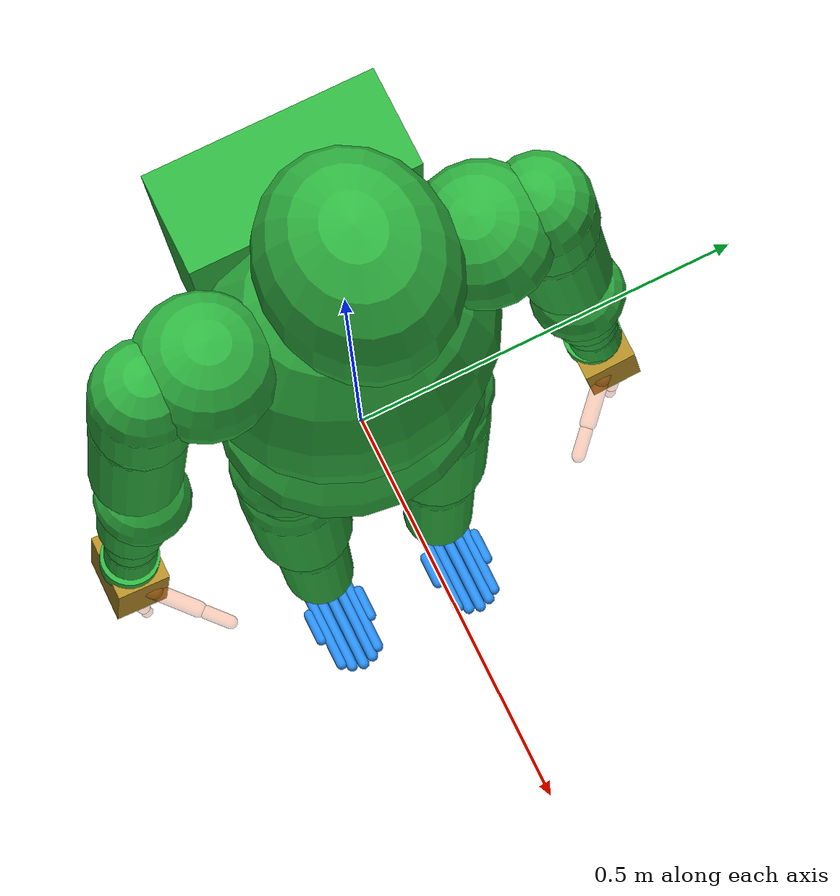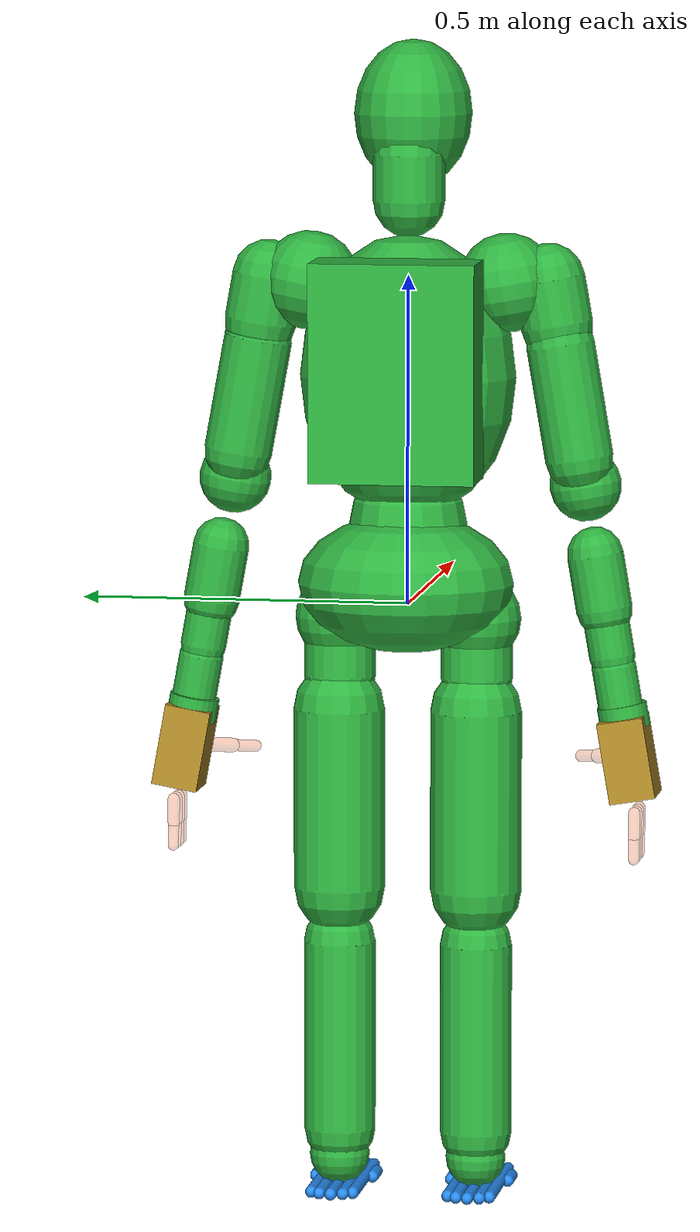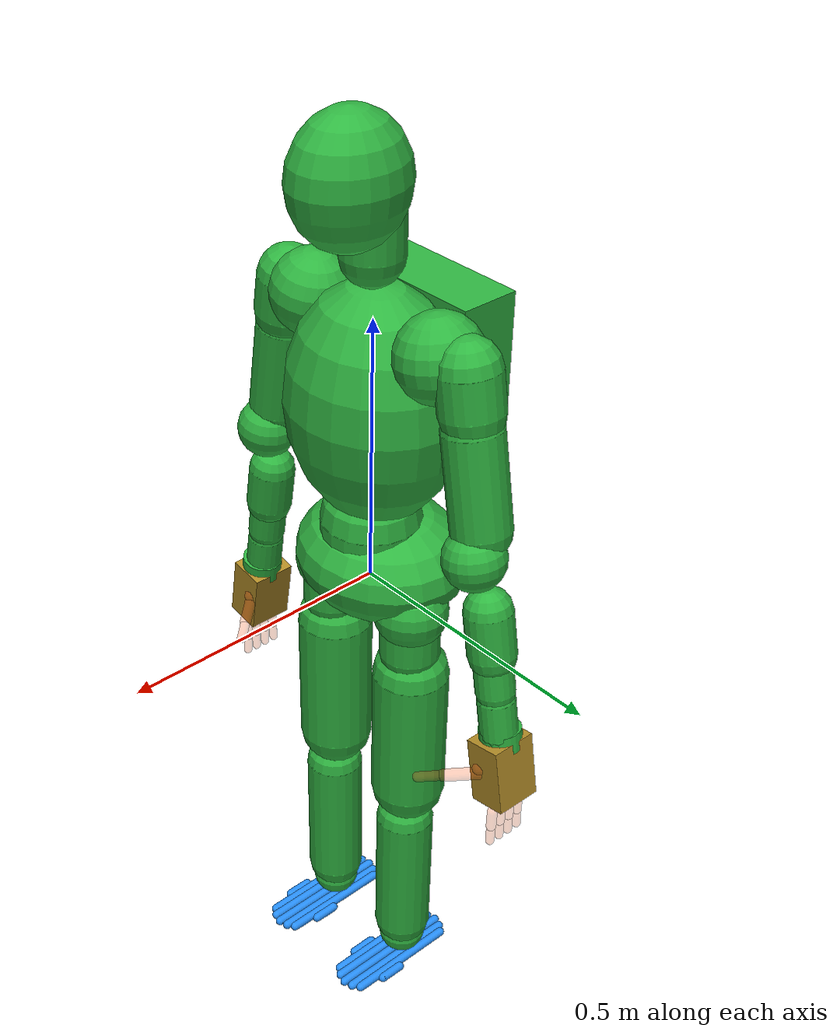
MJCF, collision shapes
<?xml version='1.0' encoding='UTF-8'?>
<mujoco model="walker_s2_dynamics_symmetry_corrected">
  <compiler angle="radian" meshdir="assets/" autolimits="true" inertiafromgeom="false"/>
  <option timestep="0.002" integrator="implicitfast" solver="Newton" cone="pyramidal"/>
  <!-- actuator user[0:5] = rated_torque_per_motor[Nm], peak_torque_per_motor[Nm], documented_max_speed[rad/s], physical_motor_count, documented_rated_speed[rad/s]. -->
  <size nuser_actuator="5"/>
  <default>
    <default class="s2_visual">
      <geom group="1" density="0" contype="0" conaffinity="0"/>
    </default>
    <default class="s2_body_collision">
      <geom group="3" density="0" contype="0" conaffinity="1" condim="1" margin="0" gap="0"/>
    </default>
    <default class="s2_foot_collision">
      <geom group="3" density="0" contype="0" conaffinity="1" condim="3" priority="1" friction="0.60 0.005 0.0001" margin="0" gap="0"/>
    </default>
    <default class="s2_finger_proxy">
      <geom group="4" density="0" contype="0" conaffinity="0" condim="3" friction="0.90 0.005 0.0001" margin="0" gap="0"/>
    </default>
  </default>
  <asset>
    <mesh name="base_link" file="base_link.STL"/>
    <mesh name="L_hip_roll_link" file="L_hip_roll_link.STL"/>
    <mesh name="L_hip_yaw_link" file="L_hip_yaw_link.STL"/>
    <mesh name="L_hip_pitch_link" file="L_hip_pitch_link.STL"/>
    <mesh name="L_knee_pitch_link" file="L_knee_pitch_link.STL"/>
    <mesh name="L_ankle_pitch_link" file="L_ankle_pitch_link.STL"/>
    <mesh name="L_ankle_roll_link" file="L_ankle_roll_link.STL"/>
    <mesh name="R_hip_roll_link" file="R_hip_roll_link.STL"/>
    <mesh name="R_hip_yaw_link" file="R_hip_yaw_link.STL"/>
    <mesh name="R_hip_pitch_link" file="R_hip_pitch_link.STL"/>
    <mesh name="R_knee_pitch_link" file="R_knee_pitch_link.STL"/>
    <mesh name="R_ankle_pitch_link" file="R_ankle_pitch_link.STL"/>
    <mesh name="R_ankle_roll_link" file="R_ankle_roll_link.STL"/>
    <mesh name="waist_yaw_link" file="waist_yaw_link.STL"/>
    <mesh name="waist_pitch_link" file="waist_pitch_link.STL"/>
    <mesh name="head_yaw_link" file="head_yaw_link.STL"/>
    <mesh name="head_pitch_link" file="head_pitch_link.STL"/>
    <mesh name="L_shoulder_pitch_link" file="L_shoulder_pitch_link.STL"/>
    <mesh name="L_shoulder_roll_link" file="L_shoulder_roll_link.STL"/>
    <mesh name="L_shoulder_yaw_link" file="L_shoulder_yaw_link.STL"/>
    <mesh name="L_elbow_roll_link" file="L_elbow_roll_link.STL"/>
    <mesh name="L_elbow_yaw_link" file="L_elbow_yaw_link.STL"/>
    <mesh name="L_wrist_pitch_link" file="L_wrist_pitch_link.STL"/>
    <mesh name="L_wrist_roll_link" file="L_wrist_roll_link.STL"/>
    <mesh name="L_sixforce_link" file="L_sixforce_link.STL"/>
    <mesh name="L_hand_base_link" file="L_hand_base_link.STL"/>
    <mesh name="L_palm_link" file="L_palm_link.STL"/>
    <mesh name="L_thumb_cmp_link" file="L_thumb_cmp_link.STL"/>
    <mesh name="L_thumb_mpp_link" file="L_thumb_mpp_link.STL"/>
    <mesh name="L_thumb_ip_link" file="L_thumb_ip_link.STL"/>
    <mesh name="L_index_mpp_link" file="L_index_mpp_link.STL"/>
    <mesh name="L_index_ip_link" file="L_index_ip_link.STL"/>
    <mesh name="L_middle_mpp_link" file="L_middle_mpp_link.STL"/>
    <mesh name="L_middle_ip_link" file="L_middle_ip_link.STL"/>
    <mesh name="L_ring_mpp_link" file="L_ring_mpp_link.STL"/>
    <mesh name="L_ring_ip_link" file="L_ring_ip_link.STL"/>
    <mesh name="L_little_mpp_link" file="L_little_mpp_link.STL"/>
    <mesh name="L_little_ip_link" file="L_little_ip_link.STL"/>
    <mesh name="R_shoulder_pitch_link" file="R_shoulder_pitch_link.STL"/>
    <mesh name="R_shoulder_roll_link" file="R_shoulder_roll_link.STL"/>
    <mesh name="R_shoulder_yaw_link" file="R_shoulder_yaw_link.STL"/>
    <mesh name="R_elbow_roll_link" file="R_elbow_roll_link.STL"/>
    <mesh name="R_elbow_yaw_link" file="R_elbow_yaw_link.STL"/>
    <mesh name="R_wrist_pitch_link" file="R_wrist_pitch_link.STL"/>
    <mesh name="R_wrist_roll_link" file="R_wrist_roll_link.STL"/>
    <mesh name="R_sixforce_link" file="R_sixforce_link.STL"/>
    <mesh name="R_hand_base_link" file="R_hand_base_link.STL"/>
    <mesh name="R_palm_link" file="R_palm_link.STL"/>
    <mesh name="R_thumb_cmp_link" file="R_thumb_cmp_link.STL"/>
    <mesh name="R_thumb_mpp_link" file="R_thumb_mpp_link.STL"/>
    <mesh name="R_thumb_ip_link" file="R_thumb_ip_link.STL"/>
    <mesh name="R_index_mpp_link" file="R_index_mpp_link.STL"/>
    <mesh name="R_index_ip_link" file="R_index_ip_link.STL"/>
    <mesh name="R_middle_mpp_link" file="R_middle_mpp_link.STL"/>
    <mesh name="R_middle_ip_link" file="R_middle_ip_link.STL"/>
    <mesh name="R_ring_mpp_link" file="R_ring_mpp_link.STL"/>
    <mesh name="R_ring_ip_link" file="R_ring_ip_link.STL"/>
    <mesh name="R_little_mpp_link" file="R_little_mpp_link.STL"/>
    <mesh name="R_little_ip_link" file="R_little_ip_link.STL"/>
    <material name="base_link_mat" rgba="0.7529 0.7529 0.7529 1" specular="0"/>
    <material name="L_hip_roll_link_mat" rgba="0.7922 0.8196 0.9333 1" specular="0"/>
    <material name="L_hip_yaw_link_mat" rgba="0.7922 0.8196 0.9333 1" specular="0"/>
    <material name="L_hip_pitch_link_mat" rgba="1 1 1 1" specular="0"/>
    <material name="L_knee_pitch_link_mat" rgba="1 1 1 1" specular="0"/>
    <material name="L_ankle_pitch_link_mat" rgba="0.7529 0.7529 0.7529 1" specular="0"/>
    <material name="L_ankle_roll_link_mat" rgba="1 1 1 1" specular="0"/>
    <material name="R_hip_roll_link_mat" rgba="0.7922 0.8196 0.9333 1" specular="0"/>
    <material name="R_hip_yaw_link_mat" rgba="0.7922 0.8196 0.9333 1" specular="0"/>
    <material name="R_hip_pitch_link_mat" rgba="1 1 1 1" specular="0"/>
    <material name="R_knee_pitch_link_mat" rgba="1 1 1 1" specular="0"/>
    <material name="R_ankle_pitch_link_mat" rgba="0.7529 0.7529 0.7529 1" specular="0"/>
    <material name="R_ankle_roll_link_mat" rgba="1 1 1 1" specular="0"/>
    <material name="waist_yaw_link_mat" rgba="0.898 0.9177 0.9294 1" specular="0"/>
    <material name="waist_pitch_link_mat" rgba="1 1 1 1" specular="0"/>
    <material name="head_yaw_link_mat" rgba="0.7529 0.7529 0.7529 1" specular="0"/>
    <material name="head_pitch_link_mat" rgba="1 1 1 1" specular="0"/>
    <material name="L_shoulder_pitch_link_mat" rgba="0.7922 0.8196 0.9333 1" specular="0"/>
    <material name="L_shoulder_roll_link_mat" rgba="0.898 0.9177 0.9294 1" specular="0"/>
    <material name="L_shoulder_yaw_link_mat" rgba="0.898 0.9177 0.9294 1" specular="0"/>
    <material name="L_elbow_roll_link_mat" rgba="0.898 0.9177 0.9294 1" specular="0"/>
    <material name="L_elbow_yaw_link_mat" rgba="0.898 0.9177 0.9294 1" specular="0"/>
    <material name="L_wrist_pitch_link_mat" rgba="0.7922 0.8196 0.9333 1" specular="0"/>
    <material name="L_wrist_roll_link_mat" rgba="0.9373 1 0.0275 0.349" specular="0"/>
    <material name="L_wrist_roll_link_geom_1_mat" rgba="0.898 0.9177 0.9294 1" specular="0"/>
    <material name="L_wrist_roll_link_geom_2_mat" rgba="0.7922 0.8196 0.9333 1" specular="0"/>
    <material name="L_hand_base_link_mat" rgba="0.7922 0.8196 0.9333 1" specular="0"/>
    <material name="L_palm_link_mat" rgba="0.7529 0.7529 0.7529 1" specular="0"/>
    <material name="L_thumb_cmp_link_mat" rgba="0.7529 0.7529 0.7529 1" specular="0"/>
    <material name="L_thumb_mpp_link_mat" rgba="0.7529 0.7529 0.7529 1" specular="0"/>
    <material name="L_thumb_ip_link_mat" rgba="0.7529 0.7529 0.7529 1" specular="0"/>
    <material name="L_index_mpp_link_mat" rgba="0.7529 0.7529 0.7529 1" specular="0"/>
    <material name="L_index_ip_link_mat" rgba="0.7529 0.7529 0.7529 1" specular="0"/>
    <material name="L_middle_mpp_link_mat" rgba="0.7529 0.7529 0.7529 1" specular="0"/>
    <material name="L_middle_ip_link_mat" rgba="0.7529 0.7529 0.7529 1" specular="0"/>
    <material name="L_ring_mpp_link_mat" rgba="0.7529 0.7529 0.7529 1" specular="0"/>
    <material name="L_ring_ip_link_mat" rgba="0.7529 0.7529 0.7529 1" specular="0"/>
    <material name="L_little_mpp_link_mat" rgba="0.7529 0.7529 0.7529 1" specular="0"/>
    <material name="L_little_ip_link_mat" rgba="0.7529 0.7529 0.7529 1" specular="0"/>
    <material name="R_shoulder_pitch_link_mat" rgba="0.7922 0.8196 0.9333 1" specular="0"/>
    <material name="R_shoulder_roll_link_mat" rgba="0.898 0.9177 0.9294 1" specular="0"/>
    <material name="R_shoulder_yaw_link_mat" rgba="0.898 0.9177 0.9294 1" specular="0"/>
    <material name="R_elbow_roll_link_mat" rgba="0.898 0.9177 0.9294 1" specular="0"/>
    <material name="R_elbow_yaw_link_mat" rgba="0.898 0.9177 0.9294 1" specular="0"/>
    <material name="R_wrist_pitch_link_mat" rgba="0.7922 0.8196 0.9333 1" specular="0"/>
    <material name="R_wrist_roll_link_mat" rgba="0.9373 1 0.0275 0.349" specular="0"/>
    <material name="R_wrist_roll_link_geom_1_mat" rgba="0.898 0.9177 0.9294 1" specular="0"/>
    <material name="R_wrist_roll_link_geom_2_mat" rgba="0.7922 0.8196 0.9333 1" specular="0"/>
    <material name="R_hand_base_link_mat" rgba="0.7922 0.8196 0.9333 1" specular="0"/>
    <material name="R_palm_link_mat" rgba="0.7529 0.7529 0.7529 1" specular="0"/>
    <material name="R_thumb_cmp_link_mat" rgba="0.7529 0.7529 0.7529 1" specular="0"/>
    <material name="R_thumb_mpp_link_mat" rgba="0.7529 0.7529 0.7529 1" specular="0"/>
    <material name="R_thumb_ip_link_mat" rgba="0.7529 0.7529 0.7529 1" specular="0"/>
    <material name="R_index_mpp_link_mat" rgba="0.7529 0.7529 0.7529 1" specular="0"/>
    <material name="R_index_ip_link_mat" rgba="0.7529 0.7529 0.7529 1" specular="0"/>
    <material name="R_middle_mpp_link_mat" rgba="0.7529 0.7529 0.7529 1" specular="0"/>
    <material name="R_middle_ip_link_mat" rgba="0.7529 0.7529 0.7529 1" specular="0"/>
    <material name="R_ring_mpp_link_mat" rgba="0.7529 0.7529 0.7529 1" specular="0"/>
    <material name="R_ring_ip_link_mat" rgba="0.7529 0.7529 0.7529 1" specular="0"/>
    <material name="R_little_mpp_link_mat" rgba="0.7529 0.7529 0.7529 1" specular="0"/>
    <material name="R_little_ip_link_mat" rgba="0.7529 0.7529 0.7529 1" specular="0"/>
  </asset>
  <worldbody>
    <body name="base_link" pos="0 0 0">
      <site name="body_imu" pos="0 0 0" size="0.01"/>
      <freejoint name="world_joint"/>
      <inertial pos="-0.063865 -0.0001135 0.010653" mass="6.3977887" quat="-0.4352257 -0.4357817 0.5582897 -0.5558646" diaginertia="0.0740697 0.0551458 0.0288325"/>
      <geom pos="0 0 0" material="base_link_mat" type="mesh" mesh="base_link" class="s2_visual"/>
      <body name="L_hip_roll_link" pos="0 0.105 0">
        <joint name="L_hip_roll_joint" type="hinge" axis="1 0 0" limited="true" range="-0.4014 0.7679" damping="0" frictionloss="0" armature="0"/>
        <inertial pos="-0.00148155 2.835e-05 -0.0041073" mass="1.32123328" fullinertia="0.000385622538908 0.000416177642454 0.000505299818637 -5.84447989704e-07 1.47211953406e-07 -2.8216489716e-09"/>
        <geom pos="0 0 0" material="L_hip_roll_link_mat" type="mesh" mesh="L_hip_roll_link" class="s2_visual"/>
        <body name="L_hip_yaw_link" pos="0 0 -0.0365">
          <joint name="L_hip_yaw_joint" type="hinge" axis="0 0 -1" limited="true" range="-1.0472 0.7854" damping="0" frictionloss="0" armature="0"/>
          <inertial pos="0 -0.0075 -0.108566" mass="0.98450062" fullinertia="0.0021138 0.0024843 0.0014629 0 0 0"/>
          <geom pos="0 0 0" material="L_hip_yaw_link_mat" type="mesh" mesh="L_hip_yaw_link" class="s2_visual"/>
          <body name="L_hip_pitch_link" pos="0 0 -0.0855">
            <joint name="L_hip_pitch_joint" type="hinge" axis="0 -1 0" limited="true" range="-0.5236 1.9024" damping="0" frictionloss="0" armature="0"/>
            <inertial pos="-0.0026482 0.00250025 -0.147295" mass="4.157285075" fullinertia="0.0111253239951 0.00982924957175 0.00204452643312 1.97238835503e-05 -0.000484153284442 -0.000152725547997"/>
            <geom pos="0 0 0" material="L_hip_pitch_link_mat" type="mesh" mesh="L_hip_pitch_link" class="s2_visual"/>
            <body name="L_knee_pitch_link" pos="0 0 -0.36">
              <joint name="L_knee_pitch_joint" type="hinge" axis="0 -1 0" limited="true" range="-2.2515 0.0524" damping="0" frictionloss="0" armature="0"/>
              <inertial pos="-0.01025205 0.00147175 -0.1860935" mass="3.77348222" fullinertia="0.0021609220821 0.00199074435811 0.000397933559793 1.10083195663e-05 -3.47983583348e-05 0.000103523517385"/>
              <geom pos="0 0 0" material="L_knee_pitch_link_mat" type="mesh" mesh="L_knee_pitch_link" class="s2_visual"/>
              <body name="L_ankle_pitch_link" pos="0 0 -0.37">
                <!-- Virtual ankle coordinate; hardware uses inside/outside drivers. Do not deploy without an identified transmission map. -->
                <joint name="L_ankle_pitch_joint" type="hinge" axis="0 -1 0" limited="true" range="-0.5235 1.0471" damping="0" frictionloss="0" armature="0"/>
                <inertial pos="5.00000000001e-08 0 1.50000000004e-07" mass="0.065913875" fullinertia="5.80000000368e-06 5.80000000285e-06 8.09999999347e-06 -3.02527809642e-15 -5.70105354179e-11 6.94748076118e-11"/>
                <geom pos="0 0 0" material="L_ankle_pitch_link_mat" type="mesh" mesh="L_ankle_pitch_link" class="s2_visual"/>
                <body name="L_ankle_roll_link" pos="0 0 0">
                  <!-- Virtual ankle coordinate; hardware uses inside/outside drivers. Do not deploy without an identified transmission map. -->
                  <joint name="L_ankle_roll_joint" type="hinge" axis="1 0 0" limited="true" range="-0.5235 0.5235" damping="0" frictionloss="0" armature="0"/>
                  <inertial pos="0.036118 0 -0.03046165" mass="1.0616" fullinertia="0.000986118322847 0.00426499999134 0.00506458168582 0 -0.00017053578436 0"/>
                  <geom pos="0 0 0" material="L_ankle_roll_link_mat" type="mesh" mesh="L_ankle_roll_link" class="s2_visual"/>
                  <site name="L_foot" pos="0.030 0 -0.045" size="0.010" group="5" rgba="1 0 0 1"/>
                  <site name="left_foot" pos="0.03 0 -0.055" size="0.010" group="5" rgba="1 0 0 1"/>
                  <site name="left_sole" pos="0.030 0 -0.055" size="0.006" group="5" rgba="1 0.2 0.2 1"/>
                  <site name="L_toe" pos="0.145 0 -0.055" size="0.007" group="5" rgba="1 0.4 0 1"/>
                  <site name="L_heel" pos="-0.085 0 -0.055" size="0.007" group="5" rgba="0.4 0.4 1 1"/>
                  <geom rgba="0.15 0.55 0.95 0.34" name="L_foot1_collision" type="capsule" fromto="0.090 -0.044 -0.046 0.045 -0.044 -0.046" size="0.009" class="s2_foot_collision"/>
                  <geom rgba="0.15 0.55 0.95 0.34" name="L_foot2_collision" type="capsule" fromto="-0.080 -0.032 -0.046 0.140 -0.032 -0.046" size="0.009" class="s2_foot_collision"/>
                  <geom rgba="0.15 0.55 0.95 0.34" name="L_foot3_collision" type="capsule" fromto="-0.090 -0.018 -0.046 0.150 -0.018 -0.046" size="0.009" class="s2_foot_collision"/>
                  <geom rgba="0.15 0.55 0.95 0.34" name="L_foot4_collision" type="capsule" fromto="-0.095 0 -0.046 0.155 0 -0.046" size="0.009" class="s2_foot_collision"/>
                  <geom rgba="0.15 0.55 0.95 0.34" name="L_foot5_collision" type="capsule" fromto="-0.090 0.018 -0.046 0.150 0.018 -0.046" size="0.009" class="s2_foot_collision"/>
                  <geom rgba="0.15 0.55 0.95 0.34" name="L_foot6_collision" type="capsule" fromto="-0.080 0.032 -0.046 0.140 0.032 -0.046" size="0.009" class="s2_foot_collision"/>
                  <geom rgba="0.15 0.55 0.95 0.34" name="L_foot7_collision" type="capsule" fromto="0.090 0.044 -0.046 0.045 0.044 -0.046" size="0.009" class="s2_foot_collision"/>
                </body>
                <geom rgba="0.18 0.70 0.25 0.30" name="L_ankle_pitch_collision" type="sphere" pos="0 0 0" size="0.046" class="s2_body_collision"/>
              </body>
              <geom rgba="0.18 0.70 0.25 0.30" name="L_shin_collision" type="capsule" fromto="0 0 -0.040 0 0 -0.330" size="0.055" class="s2_body_collision"/>
            </body>
            <geom rgba="0.18 0.70 0.25 0.30" name="L_thigh_collision" type="capsule" fromto="-0.005 0 -0.040 -0.005 0 -0.315" size="0.070" class="s2_body_collision"/>
          </body>
          <geom rgba="0.18 0.70 0.25 0.30" name="L_hip_yaw_collision" type="capsule" fromto="0 0 -0.005 0 0 -0.075" size="0.055" class="s2_body_collision"/>
        </body>
        <geom rgba="0.18 0.70 0.25 0.30" name="L_hip_roll_collision" type="sphere" pos="0 0 -0.020" size="0.068" class="s2_body_collision"/>
      </body>
      <body name="R_hip_roll_link" pos="0 -0.105 0">
        <joint name="R_hip_roll_joint" type="hinge" axis="1 0 0" limited="true" range="-0.7679 0.4014" damping="0" frictionloss="0" armature="0"/>
        <inertial pos="-0.00148155 -2.835e-05 -0.0041073" mass="1.32123328" fullinertia="0.000385622538908 0.000416177642454 0.000505299818637 5.84447989704e-07 1.47211953406e-07 2.8216489716e-09"/>
        <geom pos="0 0 0" material="R_hip_roll_link_mat" type="mesh" mesh="R_hip_roll_link" class="s2_visual"/>
        <body name="R_hip_yaw_link" pos="0 0 -0.0365">
          <joint name="R_hip_yaw_joint" type="hinge" axis="0 0 -1" limited="true" range="-0.7854 1.0472" damping="0" frictionloss="0" armature="0"/>
          <inertial pos="0 0.0075 -0.108566" mass="0.98450062" fullinertia="0.0021138 0.0024843 0.0014629 0 0 0"/>
          <geom pos="0 0 0" material="R_hip_yaw_link_mat" type="mesh" mesh="R_hip_yaw_link" class="s2_visual"/>
          <body name="R_hip_pitch_link" pos="0 0 -0.0855">
            <joint name="R_hip_pitch_joint" type="hinge" axis="0 -1 0" limited="true" range="-0.5236 1.9024" damping="0" frictionloss="0" armature="0"/>
            <inertial pos="-0.0026482 -0.00250025 -0.147295" mass="4.157285075" fullinertia="0.0111253239951 0.00982924957175 0.00204452643312 -1.97238835503e-05 -0.000484153284442 0.000152725547997"/>
            <geom pos="0 0 0" material="R_hip_pitch_link_mat" type="mesh" mesh="R_hip_pitch_link" class="s2_visual"/>
            <body name="R_knee_pitch_link" pos="0 0 -0.36">
              <joint name="R_knee_pitch_joint" type="hinge" axis="0 -1 0" limited="true" range="-2.2515 0.0524" damping="0" frictionloss="0" armature="0"/>
              <inertial pos="-0.01025205 -0.00147175 -0.1860935" mass="3.77348222" fullinertia="0.0021609220821 0.00199074435811 0.000397933559793 -1.10083195663e-05 -3.47983583348e-05 -0.000103523517385"/>
              <geom pos="0 0 0" material="R_knee_pitch_link_mat" type="mesh" mesh="R_knee_pitch_link" class="s2_visual"/>
              <body name="R_ankle_pitch_link" pos="0 0 -0.37">
                <!-- Virtual ankle coordinate; hardware uses inside/outside drivers. Do not deploy without an identified transmission map. -->
                <joint name="R_ankle_pitch_joint" type="hinge" axis="0 -1 0" limited="true" range="-0.5235 1.0471" damping="0" frictionloss="0" armature="0"/>
                <inertial pos="5.00000000001e-08 0 1.50000000004e-07" mass="0.065913875" fullinertia="5.80000000368e-06 5.80000000285e-06 8.09999999347e-06 3.02527809642e-15 -5.70105354179e-11 -6.94748076118e-11"/>
                <geom pos="0 0 0" material="R_ankle_pitch_link_mat" type="mesh" mesh="R_ankle_pitch_link" class="s2_visual"/>
                <body name="R_ankle_roll_link" pos="0 0 0">
                  <!-- Virtual ankle coordinate; hardware uses inside/outside drivers. Do not deploy without an identified transmission map. -->
                  <joint name="R_ankle_roll_joint" type="hinge" axis="1 0 0" limited="true" range="-0.5235 0.5235" damping="0" frictionloss="0" armature="0"/>
                  <inertial pos="0.036118 0 -0.03046165" mass="1.0616" fullinertia="0.000986118322847 0.00426499999134 0.00506458168582 0 -0.00017053578436 0"/>
                  <geom pos="0 0 0" material="R_ankle_roll_link_mat" type="mesh" mesh="R_ankle_roll_link" class="s2_visual"/>
                  <site name="R_foot" pos="0.030 0 -0.045" size="0.010" group="5" rgba="1 0 0 1"/>
                  <site name="right_foot" pos="0.03 0 -0.055" size="0.010" group="5" rgba="1 0 0 1"/>
                  <site name="right_sole" pos="0.030 0 -0.055" size="0.006" group="5" rgba="1 0.2 0.2 1"/>
                  <site name="R_toe" pos="0.145 0 -0.055" size="0.007" group="5" rgba="1 0.4 0 1"/>
                  <site name="R_heel" pos="-0.085 0 -0.055" size="0.007" group="5" rgba="0.4 0.4 1 1"/>
                  <geom rgba="0.15 0.55 0.95 0.34" name="R_foot1_collision" type="capsule" fromto="0.090 -0.044 -0.046 0.045 -0.044 -0.046" size="0.009" class="s2_foot_collision"/>
                  <geom rgba="0.15 0.55 0.95 0.34" name="R_foot2_collision" type="capsule" fromto="-0.080 -0.032 -0.046 0.140 -0.032 -0.046" size="0.009" class="s2_foot_collision"/>
                  <geom rgba="0.15 0.55 0.95 0.34" name="R_foot3_collision" type="capsule" fromto="-0.090 -0.018 -0.046 0.150 -0.018 -0.046" size="0.009" class="s2_foot_collision"/>
                  <geom rgba="0.15 0.55 0.95 0.34" name="R_foot4_collision" type="capsule" fromto="-0.095 0 -0.046 0.155 0 -0.046" size="0.009" class="s2_foot_collision"/>
                  <geom rgba="0.15 0.55 0.95 0.34" name="R_foot5_collision" type="capsule" fromto="-0.090 0.018 -0.046 0.150 0.018 -0.046" size="0.009" class="s2_foot_collision"/>
                  <geom rgba="0.15 0.55 0.95 0.34" name="R_foot6_collision" type="capsule" fromto="-0.080 0.032 -0.046 0.140 0.032 -0.046" size="0.009" class="s2_foot_collision"/>
                  <geom rgba="0.15 0.55 0.95 0.34" name="R_foot7_collision" type="capsule" fromto="0.090 0.044 -0.046 0.045 0.044 -0.046" size="0.009" class="s2_foot_collision"/>
                </body>
                <geom rgba="0.18 0.70 0.25 0.30" name="R_ankle_pitch_collision" type="sphere" pos="0 0 0" size="0.046" class="s2_body_collision"/>
              </body>
              <geom rgba="0.18 0.70 0.25 0.30" name="R_shin_collision" type="capsule" fromto="0 0 -0.040 0 0 -0.330" size="0.055" class="s2_body_collision"/>
            </body>
            <geom rgba="0.18 0.70 0.25 0.30" name="R_thigh_collision" type="capsule" fromto="-0.005 0 -0.040 -0.005 0 -0.315" size="0.070" class="s2_body_collision"/>
          </body>
          <geom rgba="0.18 0.70 0.25 0.30" name="R_hip_yaw_collision" type="capsule" fromto="0 0 -0.005 0 0 -0.075" size="0.055" class="s2_body_collision"/>
        </body>
        <geom rgba="0.18 0.70 0.25 0.30" name="R_hip_roll_collision" type="sphere" pos="0 0 -0.020" size="0.068" class="s2_body_collision"/>
      </body>
      <body name="waist_yaw_link" pos="0 0 0.0685">
        <joint name="waist_yaw_joint" type="hinge" axis="0 0 -1" limited="true" range="-2.7925 2.7925" damping="0" frictionloss="0" armature="0"/>
        <inertial pos="-0.0002965 0.0024674 -0.0399755" mass="0.51683988" quat="0.826757 0.560841 -0.025736 0.0356073" diaginertia="0.0009133 0.0008191 0.0006721"/>
        <geom pos="0 0 0" material="waist_yaw_link_mat" type="mesh" mesh="waist_yaw_link" class="s2_visual"/>
        <body name="waist_pitch_link" pos="0 0 0.0745">
          <joint name="waist_pitch_joint" type="hinge" axis="0 -1 0" limited="true" range="-1.5533 0.6109" damping="0" frictionloss="0" armature="0"/>
          <inertial pos="-0.0126777 0.0000934 0.196974" mass="23.78819178" quat="0.9999958 -0.0001383 -0.0027111 -0.0010272" diaginertia="0.0460497 0.0323486 0.0178621"/>
          <geom pos="0 0 0" material="waist_pitch_link_mat" type="mesh" mesh="waist_pitch_link" class="s2_visual"/>
          <body name="torso_link" pos="0 0 0.2">
            <!--Coordinate frame only: removed duplicate mass=1 with zero inertia.-->
          </body>
          <body name="head_yaw_link" pos="0.0031354 0 0.48409" quat="0.9999948 0 0.0032383 0">
            <joint name="head_yaw_joint" type="hinge" axis="0 0 1" limited="true" range="-1.6406 1.6406" damping="0" frictionloss="0" armature="0"/>
            <inertial pos="0.0002268 -0.0000387 0.0227083" mass="0.58109743" quat="0.5107139 0.4899289 0.5024549 0.4966689" diaginertia="0.0000468 0.0000321 0.0000288"/>
            <geom pos="0 0 0" material="head_yaw_link_mat" type="mesh" mesh="head_yaw_link" class="s2_visual"/>
            <body name="head_pitch_link" pos="0 0 0.025">
              <site name="head_imu" pos="0 0 0.025" size="0.01"/>
              <joint name="head_pitch_joint" type="hinge" axis="0 -1 0" limited="true" range="-0.6807 0.5061" damping="0" frictionloss="0" armature="0"/>
              <inertial pos="0.0493311 0.0000107 0.106461" mass="1.06900742" quat="0.9998365 0.0009409 0.0180595 0.0000238" diaginertia="0.0013512 0.000918 0.0007371"/>
              <geom pos="0 0 0" material="head_pitch_link_mat" type="mesh" mesh="head_pitch_link" class="s2_visual"/>
              <geom rgba="0.18 0.70 0.25 0.30" name="head_collision" type="ellipsoid" pos="0.045 0 0.090" size="0.105 0.090 0.112" class="s2_body_collision"/>
            </body>
            <geom rgba="0.18 0.70 0.25 0.30" name="neck_collision" type="capsule" fromto="0 0 -0.015 0 0 0.055" size="0.055" class="s2_body_collision"/>
          </body>
          <body name="L_shoulder_pitch_link" pos="-0.0023453 0.150912 0.348138" quat="0.9961945 0.0871543 0.0006622 -0.0005065">
            <joint name="L_shoulder_pitch_joint" type="hinge" axis="0 -1 0" limited="true" range="-2.8274 2.8274" damping="0" frictionloss="0" armature="0"/>
            <inertial pos="4.98137586316e-09 0.0504174 1.97122027249e-07" mass="0.961823375" fullinertia="0.000592200179034 0.000522700000084 0.000621099820882 -1.12924593196e-11 5.08633156462e-08 6.59359948984e-12"/>
            <geom pos="0 0 0" material="L_shoulder_pitch_link_mat" type="mesh" mesh="L_shoulder_pitch_link" class="s2_visual"/>
            <body name="L_shoulder_roll_link" pos="0 0.063 0">
              <joint name="L_shoulder_roll_joint" type="hinge" axis="-1 0 0" limited="true" range="-1.85 0.0873" damping="0" frictionloss="0" armature="0"/>
              <inertial pos="0.000943185030146 0.00274689774937 -0.0379571315392" mass="0.54148486" fullinertia="0.00101985334772 0.001317548498 0.000985398154274 -7.89194187233e-06 1.02217764963e-05 2.29577983477e-05"/>
              <geom pos="0 0 0" material="L_shoulder_roll_link_mat" type="mesh" mesh="L_shoulder_roll_link" class="s2_visual"/>
              <body name="L_shoulder_yaw_link" pos="0.0010004 -0.000978 -0.081729" quat="0.9999861 0.0024204 -0.0000114 -0.0046921">
                <joint name="L_shoulder_yaw_joint" type="hinge" axis="0 0 -1" limited="true" range="-2.8972 2.8972" damping="0" frictionloss="0" armature="0"/>
                <inertial pos="0.00126893400048 0.00287228671727 -0.129191978966" mass="1.99523145" fullinertia="0.00245611022973 0.00252933923336 0.000857600536914 9.61426822061e-06 -0.000199037492575 -7.92493435623e-05"/>
                <geom pos="0 0 0" material="L_shoulder_yaw_link_mat" type="mesh" mesh="L_shoulder_yaw_link" class="s2_visual"/>
                <body name="L_elbow_roll_link" pos="0.0199928 0 -0.213">
                  <joint name="L_elbow_roll_joint" type="hinge" axis="0 1 0" limited="true" range="-2.618 0" damping="0" frictionloss="0" armature="0"/>
                  <inertial pos="-0.0093317043221 -0.00056966047468 -0.0525008145353" mass="0.68765335" fullinertia="0.00163645822904 0.00121731133169 0.000996080439266 -1.38158277089e-06 0.000147033725196 -1.43467840925e-05"/>
                  <geom pos="0 0 0" material="L_elbow_roll_link_mat" type="mesh" mesh="L_elbow_roll_link" class="s2_visual"/>
                  <body name="L_elbow_yaw_link" pos="-0.0199928 0 -0.118181">
                    <joint name="L_elbow_yaw_joint" type="hinge" axis="0 0 -1" limited="true" range="-2.9147 2.9147" damping="0" frictionloss="0" armature="0"/>
                    <inertial pos="-0.00322960948846 0.000158334402139 -0.0753887182898" mass="0.858046155" fullinertia="0.000358046920725 0.000471601462593 0.000385151616682 -1.22358673141e-06 -6.30077936215e-09 5.93433911778e-06"/>
                    <geom pos="0 0 0" material="L_elbow_yaw_link_mat" type="mesh" mesh="L_elbow_yaw_link" class="s2_visual"/>
                    <body name="L_wrist_pitch_link" pos="0 0 -0.103819">
                      <joint name="L_wrist_pitch_joint" type="hinge" axis="0 -1 0" limited="true" range="-1.5882 1.5882" damping="0" frictionloss="0" armature="0"/>
                      <inertial pos="-0.00333889717762 -0.000843859669232 -0.0387217614124" mass="1.2811" fullinertia="0.00126164564195 0.00126163861166 0.000529815746395 -8.13063226853e-09 -1.26608981682e-06 -2.0393449129e-06"/>
                      <geom pos="0 0 0" material="L_wrist_pitch_link_mat" type="mesh" mesh="L_wrist_pitch_link" class="s2_visual"/>
                      <body name="L_wrist_roll_link" pos="0 0 -0.076">
                        <joint name="L_wrist_roll_joint" type="hinge" axis="-1 0 0" limited="true" range="-1.9897 1.9897" damping="0" frictionloss="0" armature="0"/>
                        <inertial pos="-0.00302986054526 -0.0496801232719 -0.0860547802444" mass="0.15277117" fullinertia="0.000766071483311 0.000377323920924 0.000692404595765 3.7764574461e-06 9.35137467419e-07 -0.000103260883006"/>
                        <geom pos="0 0 0" material="L_wrist_roll_link_mat" type="mesh" mesh="L_wrist_roll_link" class="s2_visual"/>
                        <body name="L_wrist_roll_link_geom_1" pos="0 0 0">
                          <!--Restored six-axis force-sensor housing inertia from the original Walker S2 URDF; the complete hand subtree remains downstream of this sensor body.-->
                          <inertial pos="-0.00477302519269 -0.00114013364791 -0.0724839725077" mass="0.2454098" fullinertia="7.51862712573e-05 9.34958988295e-05 0.000106017829913 -2.02353459747e-07 -1.99536892324e-06 1.27916090996e-08"/>
                          <!--Coordinate/visual helper frame only; placeholder inertial removed.-->
                          <geom pos="-0.0044948 -0.0019462 -0.0843794" quat="0.9999937 -0.0024445 0.0025736 0.0000063" material="L_wrist_roll_link_geom_1_mat" type="mesh" mesh="L_sixforce_link" class="s2_visual"/>
                          <geom rgba="0.18 0.70 0.25 0.30" name="L_sixforce_collision" type="cylinder" pos="-0.0044948 -0.0019462 -0.0843794" quat="0.9999937 -0.0024445 0.0025736 0.0000063" size="0.038 0.018" class="s2_body_collision"/>
                          <!-- Site belongs to the welded sensor child body; force/torque therefore measures the complete hand subtree. -->
                          <site name="L_wrist_ft" pos="-0.0044948 -0.0019462 -0.0843794" size="0.008" group="5" rgba="0 1 1 1" quat="1 0 0 0"/>
                          <body name="L_hand_base_link" pos="0 0 -0.085" quat="0.0000014 0 1 0">
                            <!--Combined hand-base+palm inertia approximated as the active collision box; replace with CAD inertia when available.-->
                            <inertial pos="0 0 0.060" mass="0.66238427" diaginertia="0.0011192086 0.0012569845 0.0006787231"/>
                            <geom pos="0 0 0" material="L_hand_base_link_mat" type="mesh" mesh="L_hand_base_link" class="s2_visual"/>
                            <body name="L_palm_link" pos="0 0 0">
                              <!--Mass transferred to parent hand_base_link; this body is retained as a kinematic frame.-->
                              <geom pos="0.000357 -0.013196 0.099778" quat="0.5 0.5 -0.499998 0.500002" material="L_palm_link_mat" type="mesh" mesh="L_palm_link" class="s2_visual"/>
                              <body name="L_thumb_cmp_link" pos="-0.0286001 -0.0058313 0.0511999" quat="0.0000028 -0.3673161 0.9300962 0.0000004">
                                <joint name="L_thumb_cmp_joint" type="hinge" axis="0 0 1" limited="true" range="-2.11 0" damping="0" frictionloss="0" armature="0"/>
                                <inertial pos="0.0056308 -0.00075 -0.0043585" mass="0.0151103" quat="0.105013 0.895844 0.0102632 0.43166" diaginertia="0.0000013 0.0000011 0.0000007"/>
                                <geom pos="0 0 0" material="L_thumb_cmp_link_mat" type="mesh" mesh="L_thumb_cmp_link" class="s2_visual"/>
                                <body name="L_thumb_mpp_link" pos="0.012 -0.0010557 -0.010045" quat="0.669137 -0.743139 0 0">
                                  <joint name="L_thumb_mpp_joint" type="hinge" axis="0 0 1" limited="true" range="0 1.85" damping="0" frictionloss="0" armature="0"/>
                                  <inertial pos="0.0361842 -0.0019502 -0.000077" mass="0.067412" quat="0.4757797 0.4734607 0.5257347 0.5225626" diaginertia="0.0000332 0.0000327 0.0000061"/>
                                  <geom pos="0 0 0" material="L_thumb_mpp_link_mat" type="mesh" mesh="L_thumb_mpp_link" class="s2_visual"/>
                                  <body name="L_thumb_ip_link" pos="0.075 -0.0000116 0">
                                    <joint name="L_thumb_ip_joint" type="hinge" axis="0 0 1" limited="true" range="0 1.09" damping="0" frictionloss="0" armature="0"/>
                                    <inertial pos="0.0135371 0.0041693 0.0000061" mass="0.0173112" quat="0.4537549 0.4537549 0.5423159 0.5423159" diaginertia="0.0000019 0.0000018 0.000001"/>
                                    <geom pos="0 0 0" material="L_thumb_ip_link_mat" type="mesh" mesh="L_thumb_ip_link" class="s2_visual"/>
                                    <geom rgba="0.95 0.35 0.10 0.28" name="L_thumb_distal_finger_collision" type="capsule" fromto="0 0 0 0.035 0 0" size="0.009" class="s2_finger_proxy"/>
                                  </body>
                                  <geom rgba="0.95 0.35 0.10 0.28" name="L_thumb_proximal_finger_collision" type="capsule" fromto="0 0 0 0.065 0 0" size="0.011" class="s2_finger_proxy"/>
                                </body>
                                <geom rgba="0.95 0.35 0.10 0.28" name="L_thumb_base_finger_collision" type="capsule" fromto="0 0 0 0.015 0 0" size="0.012" class="s2_finger_proxy"/>
                              </body>
                              <body name="L_index_mpp_link" pos="-0.0304135 -0.0015001 0.141595" quat="0.0646107 -0.6971038 0.0633213 -0.7112398">
                                <joint name="L_index_mpp_joint" type="hinge" axis="0 0 1" limited="true" range="0 1.71" damping="0" frictionloss="0" armature="0"/>
                                <inertial pos="0.0152531 -0.0018168 0.0001521" mass="0.0147008" quat="0.5 0.5 0.5 0.5" diaginertia="0.0000036 0.0000035 0.0000009"/>
                                <geom pos="0 0 0" material="L_index_mpp_link_mat" type="mesh" mesh="L_index_mpp_link" class="s2_visual"/>
                                <body name="L_index_ip_link" pos="0.0388 0 0" quat="0.9999737 0 0 -0.0072544">
                                  <joint name="L_index_ip_joint" type="hinge" axis="0 0 1" limited="true" range="0 1.76" damping="0" frictionloss="0" armature="0"/>
                                  <inertial pos="0.0168086 -0.0011753 0" mass="0.0133493" quat="0.4667631 0.4667631 0.5311612 0.5311612" diaginertia="0.0000027 0.0000026 0.0000004"/>
                                  <geom pos="0 0 0" material="L_index_ip_link_mat" type="mesh" mesh="L_index_ip_link" class="s2_visual"/>
                                  <geom rgba="0.95 0.35 0.10 0.28" name="L_index_distal_finger_collision" type="capsule" fromto="0 0 0 0.032 0 0" size="0.008" class="s2_finger_proxy"/>
                                </body>
                                <geom rgba="0.95 0.35 0.10 0.28" name="L_index_proximal_finger_collision" type="capsule" fromto="0 0 0 0.036 0 0" size="0.009" class="s2_finger_proxy"/>
                              </body>
                              <body name="L_middle_mpp_link" pos="-0.0100005 -0.0015 0.1418" quat="0.0639719 -0.7042058 0.0639665 -0.7042088">
                                <joint name="L_middle_mpp_joint" type="hinge" axis="0 0 1" limited="true" range="0 1.71" damping="0" frictionloss="0" armature="0"/>
                                <inertial pos="0.0147601 -0.0017148 0.0001287" mass="0.0143021" quat="0.4970851 0.497085 0.502898 0.5028981" diaginertia="0.0000034 0.0000034 0.0000009"/>
                                <geom pos="0 0 0" material="L_middle_mpp_link_mat" type="mesh" mesh="L_middle_mpp_link" class="s2_visual"/>
                                <body name="L_middle_ip_link" pos="0.0388 0 0" quat="0.9999818 0 0 -0.006033">
                                  <joint name="L_middle_ip_joint" type="hinge" axis="0 0 1" limited="true" range="0 1.76" damping="0" frictionloss="0" armature="0"/>
                                  <inertial pos="0.0177132 -0.0010967 0.0000256" mass="0.0148881" quat="0.4677258 0.4677257 0.5303137 0.5303137" diaginertia="0.0000035 0.0000034 0.0000004"/>
                                  <geom pos="0 0 0" material="L_middle_ip_link_mat" type="mesh" mesh="L_middle_ip_link" class="s2_visual"/>
                                  <geom rgba="0.95 0.35 0.10 0.28" name="L_middle_distal_finger_collision" type="capsule" fromto="0 0 0 0.032 0 0" size="0.008" class="s2_finger_proxy"/>
                                </body>
                                <geom rgba="0.95 0.35 0.10 0.28" name="L_middle_proximal_finger_collision" type="capsule" fromto="0 0 0 0.036 0 0" size="0.009" class="s2_finger_proxy"/>
                              </body>
                              <body name="L_ring_mpp_link" pos="0.0104125 -0.0015 0.141595" quat="0.0633268 -0.7112379 0.0646053 -0.6971059">
                                <joint name="L_ring_mpp_joint" type="hinge" axis="0 0 1" limited="true" range="0 1.71" damping="0" frictionloss="0" armature="0"/>
                                <inertial pos="0.0147595 -0.001715 0.0001287" mass="0.0143021" quat="0.4970851 0.497085 0.502898 0.5028981" diaginertia="0.0000034 0.0000034 0.0000009"/>
                                <geom pos="0 0 0" material="L_ring_mpp_link_mat" type="mesh" mesh="L_ring_mpp_link" class="s2_visual"/>
                                <body name="L_ring_ip_link" pos="0.0388 0 0" quat="0.9999737 0 0 -0.0072544">
                                  <joint name="L_ring_ip_joint" type="hinge" axis="0 0 1" limited="true" range="0 1.76" damping="0" frictionloss="0" armature="0"/>
                                  <inertial pos="0.0161543 -0.0013024 0.0000276" mass="0.0137479" quat="0.4652121 0.4652121 0.5325201 0.5325201" diaginertia="0.0000029 0.0000028 0.0000004"/>
                                  <geom pos="0 0 0" material="L_ring_ip_link_mat" type="mesh" mesh="L_ring_ip_link" class="s2_visual"/>
                                  <geom rgba="0.95 0.35 0.10 0.28" name="L_ring_distal_finger_collision" type="capsule" fromto="0 0 0 0.032 0 0" size="0.008" class="s2_finger_proxy"/>
                                </body>
                                <geom rgba="0.95 0.35 0.10 0.28" name="L_ring_proximal_finger_collision" type="capsule" fromto="0 0 0 0.036 0 0" size="0.009" class="s2_finger_proxy"/>
                              </body>
                              <body name="L_little_mpp_link" pos="0.0308175 -0.0014999 0.140981" quat="0.0626752 -0.718198 0.0652375 -0.689933">
                                <joint name="L_little_mpp_joint" type="hinge" axis="0 0 1" limited="true" range="0 1.71" damping="0" frictionloss="0" armature="0"/>
                                <inertial pos="0.0147588 -0.0017151 0.0001287" mass="0.0143021" quat="0.4970851 0.497085 0.502898 0.5028981" diaginertia="0.0000034 0.0000034 0.0000009"/>
                                <geom pos="0 0 0" material="L_little_mpp_link_mat" type="mesh" mesh="L_little_mpp_link" class="s2_visual"/>
                                <body name="L_little_ip_link" pos="0.0388 0 0" quat="0.9999737 0 0 -0.0072544">
                                  <joint name="L_little_ip_joint" type="hinge" axis="0 0 1" limited="true" range="0 1.76" damping="0" frictionloss="0" armature="0"/>
                                  <inertial pos="0.0130333 -0.0014344 0.0000295" mass="0.0117927" quat="0.4601642 0.4601642 0.5368882 0.5368882" diaginertia="0.0000018 0.0000018 0.0000003"/>
                                  <geom pos="0 0 0" material="L_little_ip_link_mat" type="mesh" mesh="L_little_ip_link" class="s2_visual"/>
                                  <geom rgba="0.95 0.35 0.10 0.28" name="L_little_distal_finger_collision" type="capsule" fromto="0 0 0 0.032 0 0" size="0.008" class="s2_finger_proxy"/>
                                </body>
                                <geom rgba="0.95 0.35 0.10 0.28" name="L_little_proximal_finger_collision" type="capsule" fromto="0 0 0 0.036 0 0" size="0.009" class="s2_finger_proxy"/>
                              </body>
                            </body>
                            <geom rgba="0.70 0.55 0.15 0.32" name="L_hand_collision" type="box" pos="0 0 0.060" size="0.043 0.035 0.062" class="s2_body_collision"/>
                          </body>
                        </body>
                        <geom rgba="0.18 0.70 0.25 0.30" name="L_wrist_roll_collision" type="capsule" fromto="0 0 -0.005 0 0 -0.075" size="0.034" class="s2_body_collision"/>
                      </body>
                      <geom rgba="0.18 0.70 0.25 0.30" name="L_wrist_pitch_collision" type="capsule" fromto="0 0 -0.005 0 0 -0.065" size="0.035" class="s2_body_collision"/>
                    </body>
                    <geom rgba="0.18 0.70 0.25 0.30" name="L_forearm_collision" type="capsule" fromto="0 0 -0.012 0 0 -0.095" size="0.043" class="s2_body_collision"/>
                  </body>
                  <geom rgba="0.18 0.70 0.25 0.30" name="L_elbow_collision" type="sphere" pos="0 0 -0.025" size="0.055" class="s2_body_collision"/>
                </body>
                <geom rgba="0.18 0.70 0.25 0.30" name="L_upper_arm_collision" type="capsule" fromto="0 0 -0.020 0 0 -0.195" size="0.052" class="s2_body_collision"/>
              </body>
              <geom rgba="0.18 0.70 0.25 0.30" name="L_shoulder_roll_collision" type="capsule" fromto="0 0 -0.005 0 0 -0.075" size="0.055" class="s2_body_collision"/>
            </body>
            <geom rgba="0.18 0.70 0.25 0.30" name="L_shoulder_pitch_collision" type="sphere" pos="0 0 0" size="0.075" class="s2_body_collision"/>
          </body>
          <body name="R_shoulder_pitch_link" pos="-0.0023453 -0.150912 0.348138" quat="0.9961918 -0.087155 0.0024155 0.0003532">
            <joint name="R_shoulder_pitch_joint" type="hinge" axis="0 1 0" limited="true" range="-2.8274 2.8274" damping="0" frictionloss="0" armature="0"/>
            <inertial pos="-4.99147539745e-09 -0.0504174 2.02860420651e-07" mass="0.961823375" fullinertia="0.000592200179034 0.000522700000084 0.000621099820882 -1.48117627908e-12 -5.08633542411e-08 4.62335624776e-12"/>
            <geom pos="0 0 0" material="R_shoulder_pitch_link_mat" type="mesh" mesh="R_shoulder_pitch_link" class="s2_visual"/>
            <body name="R_shoulder_roll_link" pos="0 -0.063 0">
              <joint name="R_shoulder_roll_joint" type="hinge" axis="1 0 0" limited="true" range="-1.85 0.0873" damping="0" frictionloss="0" armature="0"/>
              <inertial pos="0.00107677527087 -0.00274690225505 -0.0379535689393" mass="0.54148486" fullinertia="0.00101978096339 0.00131754848986 0.000985470546752 7.97275985089e-06 1.03427987665e-05 -2.29299162692e-05"/>
              <geom pos="0 0 0" material="R_shoulder_roll_link_mat" type="mesh" mesh="R_shoulder_roll_link" class="s2_visual"/>
              <body name="R_shoulder_yaw_link" pos="-0.0033173 -0.0009421 -0.0843104" quat="0.9999831 0.0024281 -0.0000128 -0.0052894">
                <joint name="R_shoulder_yaw_joint" type="hinge" axis="0 0 -1" limited="true" range="-2.8972 2.8972" damping="0" frictionloss="0" armature="0"/>
                <inertial pos="0.00637798387443 -0.00211284122918 -0.126576974952" mass="1.99523145" fullinertia="0.00245795266355 0.00253022370469 0.000854873631756 -1.32199018652e-05 -0.000194672096847 5.90530714707e-05"/>
                <geom pos="0 0 0" material="R_shoulder_yaw_link_mat" type="mesh" mesh="R_shoulder_yaw_link" class="s2_visual"/>
                <body name="R_elbow_roll_link" pos="0.0199928 0 -0.213">
                  <joint name="R_elbow_roll_joint" type="hinge" axis="0 1 0" limited="true" range="-2.618 0" damping="0" frictionloss="0" armature="0"/>
                  <inertial pos="-0.00338187710437 0.000403609762071 -0.0509955587668" mass="0.68765335" fullinertia="0.00163514721634 0.00121775022236 0.000996952561303 1.11375159839e-05 0.000148920060175 1.63259915184e-05"/>
                  <geom pos="0 0 0" material="R_elbow_roll_link_mat" type="mesh" mesh="R_elbow_roll_link" class="s2_visual"/>
                  <body name="R_elbow_yaw_link" pos="-0.0199928 0 -0.118181">
                    <joint name="R_elbow_yaw_joint" type="hinge" axis="0 0 -1" limited="true" range="-2.9147 2.9147" damping="0" frictionloss="0" armature="0"/>
                    <inertial pos="0.00324407048879 -0.00139833109828 -0.0739244363053" mass="0.858046155" fullinertia="0.000358046239815 0.000471533732769 0.000385220027415 -1.19470906644e-06 3.07191941987e-08 -6.41228933727e-06"/>
                    <geom pos="0 0 0" material="R_elbow_yaw_link_mat" type="mesh" mesh="R_elbow_yaw_link" class="s2_visual"/>
                    <body name="R_wrist_pitch_link" pos="0 0 -0.103819">
                      <joint name="R_wrist_pitch_joint" type="hinge" axis="0 1 0" limited="true" range="-1.5882 1.5882" damping="0" frictionloss="0" armature="0"/>
                      <inertial pos="0.00335363641852 -0.000767883292043 -0.0372619978847" mass="1.2811" fullinertia="0.00126164528872 0.0012616389658 0.000529815745483 8.27414289434e-09 1.30979511373e-06 -2.01138763707e-06"/>
                      <geom pos="0 0 0" material="R_wrist_pitch_link_mat" type="mesh" mesh="R_wrist_pitch_link" class="s2_visual"/>
                      <body name="R_wrist_roll_link" pos="0 0 -0.076">
                        <joint name="R_wrist_roll_joint" type="hinge" axis="1 0 0" limited="true" range="-1.9897 1.9897" damping="0" frictionloss="0" armature="0"/>
                        <inertial pos="0.00305505595268 0.0473850092387 -0.0848634520475" mass="0.15277117" fullinertia="0.000766062561783 0.000378486023279 0.000691251414938 4.20002374832e-06 -1.04255902221e-06 0.000104998533157"/>
                        <geom pos="0 0 0" material="R_wrist_roll_link_mat" type="mesh" mesh="R_wrist_roll_link" class="s2_visual"/>
                        <body name="R_wrist_roll_link_geom_1" pos="0 0 0">
                          <!--Restored six-axis force-sensor housing inertia from the original Walker S2 URDF; the complete hand subtree remains downstream of this sensor body.-->
                          <inertial pos="0.00230635182884 -0.00110590231254 -0.0710284609966" mass="0.2454098" fullinertia="7.52007014659e-05 9.34959007596e-05 0.000106003397774 -2.0239701117e-07 -2.10385610262e-06 1.24245913589e-08"/>
                          <!--Coordinate/visual helper frame only; placeholder inertial removed.-->
                          <geom pos="0.0022054 -0.0019134 -0.0818061" quat="0.999997 -0.0024367 0 0" material="R_wrist_roll_link_geom_1_mat" type="mesh" mesh="R_sixforce_link" class="s2_visual"/>
                          <geom rgba="0.18 0.70 0.25 0.30" name="R_sixforce_collision" type="cylinder" pos="0.0022054 -0.0019134 -0.0818061" quat="0.999997 -0.0024367 0 0" size="0.038 0.018" class="s2_body_collision"/>
                          <!-- Site belongs to the welded sensor child body; force/torque therefore measures the complete hand subtree. -->
                          <site name="R_wrist_ft" pos="0.0022054 -0.0019134 -0.0818061" size="0.008" group="5" rgba="0 1 1 1" quat="1 0 0 0"/>
                          <body name="R_hand_base_link" pos="0 0 -0.085" quat="0 0.9999997 0.0007963 0.0000014">
                            <!-- add diaginertia -->
                            <!--Combined hand-base+palm inertia approximated as the active collision box; replace with CAD inertia when available.-->
                            <inertial pos="0 0 0.060" mass="0.66238427" diaginertia="0.0011192086 0.0012569845 0.0006787231"/>
                            <geom pos="0 0 0" material="R_hand_base_link_mat" type="mesh" mesh="R_hand_base_link" class="s2_visual"/>
                            <body name="R_palm_link" pos="0 0 0">
                              <!--Mass transferred to parent hand_base_link; this body is retained as a kinematic frame.-->
                              <geom pos="0.000357 -0.013196 0.099778" quat="0.5 0.5 -0.499998 0.500002" material="R_palm_link_mat" type="mesh" mesh="R_palm_link" class="s2_visual"/>
                              <body name="R_thumb_cmp_link" pos="0.0293132 -0.0058311 0.0512001" quat="0.0000017 -0.9300973 0.3673131 -0.0000007">
                                <joint name="R_thumb_cmp_joint" type="hinge" axis="0 0 1" limited="true" range="0 2.11" damping="0" frictionloss="0" armature="0"/>
                                <inertial pos="0.0056308 0.00075 -0.0043585" mass="0.0151103" quat="0.105013 -0.895844 0.0102632 -0.43166" diaginertia="0.0000013 0.0000011 0.0000007"/>
                                <geom pos="0 0 0" material="R_thumb_cmp_link_mat" type="mesh" mesh="R_thumb_cmp_link" class="s2_visual"/>
                                <body name="R_thumb_mpp_link" pos="0.012 0.0010557 -0.010045" quat="0.7431372 -0.6691391 -0.0000519 -0.0000576">
                                  <joint name="R_thumb_mpp_joint" type="hinge" axis="0 0 1" limited="true" range="0 1.85" damping="0" frictionloss="0" armature="0"/>
                                  <inertial pos="0.0361842 -0.0019502 0.000077" mass="0.067412" quat="0.4734607 0.4757797 0.5225627 0.5257346" diaginertia="0.0000332 0.0000327 0.0000061"/>
                                  <geom pos="0 0 0" material="R_thumb_mpp_link_mat" type="mesh" mesh="R_thumb_mpp_link" class="s2_visual"/>
                                  <body name="R_thumb_ip_link" pos="0.075 0 0" quat="0.9999818 0 0 0.006041">
                                    <joint name="R_thumb_ip_joint" type="hinge" axis="0 0 1" limited="true" range="0 1.09" damping="0" frictionloss="0" armature="0"/>
                                    <inertial pos="0.0135371 0.0041693 -0.0000061" mass="0.0173112" quat="0.4537549 0.4537549 0.5423159 0.5423159" diaginertia="0.0000019 0.0000018 0.000001"/>
                                    <geom pos="0 0 0" material="R_thumb_ip_link_mat" type="mesh" mesh="R_thumb_ip_link" class="s2_visual"/>
                                    <geom rgba="0.95 0.35 0.10 0.28" name="R_thumb_distal_finger_collision" type="capsule" fromto="0 0 0 0.035 0 0" size="0.009" class="s2_finger_proxy"/>
                                  </body>
                                  <geom rgba="0.95 0.35 0.10 0.28" name="R_thumb_proximal_finger_collision" type="capsule" fromto="0 0 0 0.065 0 0" size="0.011" class="s2_finger_proxy"/>
                                </body>
                                <geom rgba="0.95 0.35 0.10 0.28" name="R_thumb_base_finger_collision" type="capsule" fromto="0 0 0 0.015 0 0" size="0.012" class="s2_finger_proxy"/>
                              </body>
                              <body name="R_index_mpp_link" pos="0.0311268 -0.0014999 0.141596" quat="0.0633268 -0.7112379 0.0646053 -0.6971059">
                                <joint name="R_index_mpp_joint" type="hinge" axis="0 0 1" limited="true" range="0 1.71" damping="0" frictionloss="0" armature="0"/>
                                <inertial pos="0.0152531 -0.0018168 -0.0001521" mass="0.0147008" quat="0.5 0.5 0.5 0.5" diaginertia="0.0000036 0.0000035 0.0000009"/>
                                <geom pos="0 0 0" material="R_index_mpp_link_mat" type="mesh" mesh="R_index_mpp_link" class="s2_visual"/>
                                <body name="R_index_ip_link" pos="0.0388 0 0" quat="0.9999737 0 0 -0.0072544">
                                  <joint name="R_index_ip_joint" type="hinge" axis="0 0 1" limited="true" range="0 1.76" damping="0" frictionloss="0" armature="0"/>
                                  <inertial pos="0.0168086 -0.0011753 0" mass="0.0133493" quat="0.4667631 0.4667631 0.5311612 0.5311612" diaginertia="0.0000027 0.0000026 0.0000004"/>
                                  <geom pos="0 0 0" material="R_index_ip_link_mat" type="mesh" mesh="R_index_ip_link" class="s2_visual"/>
                                  <geom rgba="0.95 0.35 0.10 0.28" name="R_index_distal_finger_collision" type="capsule" fromto="0 0 0 0.032 0 0" size="0.008" class="s2_finger_proxy"/>
                                </body>
                                <geom rgba="0.95 0.35 0.10 0.28" name="R_index_proximal_finger_collision" type="capsule" fromto="0 0 0 0.036 0 0" size="0.009" class="s2_finger_proxy"/>
                              </body>
                              <body name="R_middle_mpp_link" pos="0.0114638 -0.0015 0.1418" quat="0.0633637 -0.697357 0.0645644 -0.710992">
                                <joint name="R_middle_mpp_joint" type="hinge" axis="0 0 1" limited="true" range="0 1.71" damping="0" frictionloss="0" armature="0"/>
                                <inertial pos="0.0147601 -0.0017148 -0.0001287" mass="0.0143021" quat="0.4970851 0.497085 0.502898 0.5028981" diaginertia="0.0000034 0.0000034 0.0000009"/>
                                <geom pos="0 0 0" material="R_middle_mpp_link_mat" type="mesh" mesh="R_middle_mpp_link" class="s2_visual"/>
                                <body name="R_middle_ip_link" pos="0.038807 0 0" quat="0.999935 0.0000584 -0.0096774 -0.0060326">
                                  <joint name="R_middle_ip_joint" type="hinge" axis="0 0 1" limited="true" range="0 1.76" damping="0" frictionloss="0" armature="0"/>
                                  <inertial pos="0.0177132 -0.0010967 -0.0000256" mass="0.0148881" quat="0.4677258 0.4677257 0.5303137 0.5303137" diaginertia="0.0000035 0.0000034 0.0000004"/>
                                  <geom pos="0 0 0" material="R_middle_ip_link_mat" type="mesh" mesh="R_middle_ip_link" class="s2_visual"/>
                                  <geom rgba="0.95 0.35 0.10 0.28" name="R_middle_distal_finger_collision" type="capsule" fromto="0 0 0 0.032 0 0" size="0.008" class="s2_finger_proxy"/>
                                </body>
                                <geom rgba="0.95 0.35 0.10 0.28" name="R_middle_proximal_finger_collision" type="capsule" fromto="0 0 0 0.036 0 0" size="0.009" class="s2_finger_proxy"/>
                              </body>
                              <body name="R_ring_mpp_link" pos="-0.0097002 -0.0015 0.141596" quat="0.0646107 -0.6971038 0.0633213 -0.7112398">
                                <joint name="R_ring_mpp_joint" type="hinge" axis="0 0 1" limited="true" range="0 1.71" damping="0" frictionloss="0" armature="0"/>
                                <inertial pos="0.0147595 -0.001715 -0.0001287" mass="0.0143021" quat="0.4970851 0.497085 0.502898 0.5028981" diaginertia="0.0000034 0.0000034 0.0000009"/>
                                <geom pos="0 0 0" material="R_ring_mpp_link_mat" type="mesh" mesh="R_ring_mpp_link" class="s2_visual"/>
                                <body name="R_ring_ip_link" pos="0.0388 0 0" quat="0.9999737 0 0 -0.0072544">
                                  <joint name="R_ring_ip_joint" type="hinge" axis="0 0 1" limited="true" range="0 1.76" damping="0" frictionloss="0" armature="0"/>
                                  <inertial pos="0.0161543 -0.0013024 -0.0000276" mass="0.0137479" quat="0.4652121 0.4652121 0.5325201 0.5325201" diaginertia="0.0000029 0.0000028 0.0000004"/>
                                  <geom pos="0 0 0" material="R_ring_ip_link_mat" type="mesh" mesh="R_ring_ip_link" class="s2_visual"/>
                                  <geom rgba="0.95 0.35 0.10 0.28" name="R_ring_distal_finger_collision" type="capsule" fromto="0 0 0 0.032 0 0" size="0.008" class="s2_finger_proxy"/>
                                </body>
                                <geom rgba="0.95 0.35 0.10 0.28" name="R_ring_proximal_finger_collision" type="capsule" fromto="0 0 0 0.036 0 0" size="0.009" class="s2_finger_proxy"/>
                              </body>
                              <body name="R_little_mpp_link" pos="-0.0301052 -0.0015001 0.140981" quat="0.0652429 -0.6899309 0.0626698 -0.7181999">
                                <joint name="R_little_mpp_joint" type="hinge" axis="0 0 1" limited="true" range="0 1.71" damping="0" frictionloss="0" armature="0"/>
                                <inertial pos="0.0147588 -0.0017151 -0.0001287" mass="0.0143021" quat="0.4970851 0.497085 0.502898 0.5028981" diaginertia="0.0000034 0.0000034 0.0000009"/>
                                <geom pos="0 0 0" material="R_little_mpp_link_mat" type="mesh" mesh="R_little_mpp_link" class="s2_visual"/>
                                <body name="R_little_ip_link" pos="0.0388 0 0" quat="0.9999737 0 0 -0.0072544">
                                  <joint name="R_little_ip_joint" type="hinge" axis="0 0 1" limited="true" range="0 1.76" damping="0" frictionloss="0" armature="0"/>
                                  <inertial pos="0.0130333 -0.0014344 -0.0000295" mass="0.0117927" quat="0.4601642 0.4601642 0.5368882 0.5368882" diaginertia="0.0000018 0.0000018 0.0000003"/>
                                  <geom pos="0 0 0" material="R_little_ip_link_mat" type="mesh" mesh="R_little_ip_link" class="s2_visual"/>
                                  <geom rgba="0.95 0.35 0.10 0.28" name="R_little_distal_finger_collision" type="capsule" fromto="0 0 0 0.032 0 0" size="0.008" class="s2_finger_proxy"/>
                                </body>
                                <geom rgba="0.95 0.35 0.10 0.28" name="R_little_proximal_finger_collision" type="capsule" fromto="0 0 0 0.036 0 0" size="0.009" class="s2_finger_proxy"/>
                              </body>
                            </body>
                            <geom rgba="0.70 0.55 0.15 0.32" name="R_hand_collision" type="box" pos="0 0 0.060" size="0.043 0.035 0.062" class="s2_body_collision"/>
                          </body>
                        </body>
                        <geom rgba="0.18 0.70 0.25 0.30" name="R_wrist_roll_collision" type="capsule" fromto="0 0 -0.005 0 0 -0.075" size="0.034" class="s2_body_collision"/>
                      </body>
                      <geom rgba="0.18 0.70 0.25 0.30" name="R_wrist_pitch_collision" type="capsule" fromto="0 0 -0.005 0 0 -0.065" size="0.035" class="s2_body_collision"/>
                    </body>
                    <geom rgba="0.18 0.70 0.25 0.30" name="R_forearm_collision" type="capsule" fromto="0 0 -0.012 0 0 -0.095" size="0.043" class="s2_body_collision"/>
                  </body>
                  <geom rgba="0.18 0.70 0.25 0.30" name="R_elbow_collision" type="sphere" pos="0 0 -0.025" size="0.055" class="s2_body_collision"/>
                </body>
                <geom rgba="0.18 0.70 0.25 0.30" name="R_upper_arm_collision" type="capsule" fromto="0 0 -0.020 0 0 -0.195" size="0.052" class="s2_body_collision"/>
              </body>
              <geom rgba="0.18 0.70 0.25 0.30" name="R_shoulder_roll_collision" type="capsule" fromto="0 0 -0.005 0 0 -0.075" size="0.055" class="s2_body_collision"/>
            </body>
            <geom rgba="0.18 0.70 0.25 0.30" name="R_shoulder_pitch_collision" type="sphere" pos="0 0 0" size="0.075" class="s2_body_collision"/>
          </body>
          <geom rgba="0.18 0.70 0.25 0.30" name="torso_collision" type="ellipsoid" pos="-0.005 0 0.205" size="0.145 0.165 0.215" class="s2_body_collision"/>
          <geom rgba="0.18 0.70 0.25 0.30" name="backpack_collision" type="box" pos="-0.135 0 0.225" size="0.055 0.125 0.165" class="s2_body_collision"/>
        </body>
        <geom rgba="0.18 0.70 0.25 0.30" name="waist_yaw_collision" type="capsule" fromto="0 0 -0.035 0 0 0.055" size="0.090" class="s2_body_collision"/>
      </body>
      <geom rgba="0.18 0.70 0.25 0.30" name="base_link_collision" type="ellipsoid" pos="-0.025 0 0.035" size="0.145 0.165 0.105" class="s2_body_collision"/>
    </body>
  </worldbody>
  <equality>
    <!-- Four-generation hand distal joints are passive/coupled. Ratio uses the documented 100.94 deg distal motion over 98 deg proximal motion. -->
    <joint name="L_index_distal_coupling" joint1="L_index_ip_joint" joint2="L_index_mpp_joint" polycoef="0 1.0292397661 0 0 0" solref="0.01 1"/>
    <joint name="L_middle_distal_coupling" joint1="L_middle_ip_joint" joint2="L_middle_mpp_joint" polycoef="0 1.0292397661 0 0 0" solref="0.01 1"/>
    <joint name="L_ring_distal_coupling" joint1="L_ring_ip_joint" joint2="L_ring_mpp_joint" polycoef="0 1.0292397661 0 0 0" solref="0.01 1"/>
    <joint name="L_little_distal_coupling" joint1="L_little_ip_joint" joint2="L_little_mpp_joint" polycoef="0 1.0292397661 0 0 0" solref="0.01 1"/>
    <joint name="R_index_distal_coupling" joint1="R_index_ip_joint" joint2="R_index_mpp_joint" polycoef="0 1.0292397661 0 0 0" solref="0.01 1"/>
    <joint name="R_middle_distal_coupling" joint1="R_middle_ip_joint" joint2="R_middle_mpp_joint" polycoef="0 1.0292397661 0 0 0" solref="0.01 1"/>
    <joint name="R_ring_distal_coupling" joint1="R_ring_ip_joint" joint2="R_ring_mpp_joint" polycoef="0 1.0292397661 0 0 0" solref="0.01 1"/>
    <joint name="R_little_distal_coupling" joint1="R_little_ip_joint" joint2="R_little_mpp_joint" polycoef="0 1.0292397661 0 0 0" solref="0.01 1"/>
  </equality>
  <actuator>
    <!-- Active position servos. kv is computed for critical damping at the home keyframe from the model effective joint inertia. forcerange uses documented continuous/rated torque. -->
    <!-- user[0:5] = rated torque per physical motor [Nm], peak torque per physical motor [Nm], documented maximum speed [rad/s], physical motor count, documented rated speed [rad/s]. -->
    <!-- Virtual ankle pitch/roll torque limits remain an approximation; the true inside/outside motor transmission and coupled torque polytope are not available in the supplied documents. -->
    <position name="L_hip_roll_joint_servo" joint="L_hip_roll_joint" kp="110" forcelimited="true" forcerange="-75 75" ctrllimited="true" inheritrange="0.95" user="75 225 8.37758040957 1 5.23598775598" kv="17.165380585"/>
    <position name="L_hip_yaw_joint_servo" joint="L_hip_yaw_joint" kp="30" forcelimited="true" forcerange="-22 22" ctrllimited="true" inheritrange="0.95" user="22 65 8.37758040957 1 5.23598775598" kv="1.081896667"/>
    <position name="L_hip_pitch_joint_servo" joint="L_hip_pitch_joint" kp="100" forcelimited="true" forcerange="-75 75" ctrllimited="true" inheritrange="0.95" user="75 225 8.37758040957 1 5.23598775598" kv="4.8306828565"/>
    <position name="L_knee_pitch_joint_servo" joint="L_knee_pitch_joint" kp="125" forcelimited="true" forcerange="-75 75" ctrllimited="true" inheritrange="0.95" user="75 225 8.37758040957 1 5.23598775598" kv="3.880022332"/>
    <position name="L_ankle_pitch_joint_servo" joint="L_ankle_pitch_joint" kp="30" forcelimited="true" forcerange="-44 44" ctrllimited="true" inheritrange="0.95" user="22 65 8.37758040957 2 5.23598775598" kv="0.81297141475"/>
    <position name="L_ankle_roll_joint_servo" joint="L_ankle_roll_joint" kp="30" forcelimited="true" forcerange="-44 44" ctrllimited="true" inheritrange="0.95" user="22 65 8.37758040957 2 5.23598775598" kv="0.4417916051"/>
    <position name="R_hip_roll_joint_servo" joint="R_hip_roll_joint" kp="110" forcelimited="true" forcerange="-75 75" ctrllimited="true" inheritrange="0.95" user="75 225 8.37758040957 1 5.23598775598" kv="17.165380585"/>
    <position name="R_hip_yaw_joint_servo" joint="R_hip_yaw_joint" kp="30" forcelimited="true" forcerange="-22 22" ctrllimited="true" inheritrange="0.95" user="22 65 8.37758040957 1 5.23598775598" kv="1.081896667"/>
    <position name="R_hip_pitch_joint_servo" joint="R_hip_pitch_joint" kp="100" forcelimited="true" forcerange="-75 75" ctrllimited="true" inheritrange="0.95" user="75 225 8.37758040957 1 5.23598775598" kv="4.8306828565"/>
    <position name="R_knee_pitch_joint_servo" joint="R_knee_pitch_joint" kp="125" forcelimited="true" forcerange="-75 75" ctrllimited="true" inheritrange="0.95" user="75 225 8.37758040957 1 5.23598775598" kv="3.880022332"/>
    <position name="R_ankle_pitch_joint_servo" joint="R_ankle_pitch_joint" kp="30" forcelimited="true" forcerange="-44 44" ctrllimited="true" inheritrange="0.95" user="22 65 8.37758040957 2 5.23598775598" kv="0.81297141475"/>
    <position name="R_ankle_roll_joint_servo" joint="R_ankle_roll_joint" kp="30" forcelimited="true" forcerange="-44 44" ctrllimited="true" inheritrange="0.95" user="22 65 8.37758040957 2 5.23598775598" kv="0.4417916051"/>
    <position name="waist_yaw_joint_servo" joint="waist_yaw_joint" kp="125" forcelimited="true" forcerange="-35 35" ctrllimited="true" inheritrange="0.95" user="35 85 3.87463093943 1 2.09439510239" kv="6.363866115"/>
    <position name="waist_pitch_joint_servo" joint="waist_pitch_joint" kp="125" forcelimited="true" forcerange="-79 79" ctrllimited="true" inheritrange="0.95" user="79 265 2.09439510239 1 1.57079632679" kv="5.982083272"/>
    <position name="head_yaw_joint_servo" joint="head_yaw_joint" kp="100" ctrllimited="true" inheritrange="0.95" forcelimited="true" forcerange="-3 3" user="3 4.5 5.23598775598 1 3.14159265359" kv="1.088854757"/>
    <position name="head_pitch_joint_servo" joint="head_pitch_joint" kp="100" ctrllimited="true" inheritrange="0.95" forcelimited="true" forcerange="-3 3" user="3 4.5 5.23598775598 1 3.14159265359" kv="1.998828007"/>
    <position name="L_shoulder_pitch_joint_servo" joint="L_shoulder_pitch_joint" kp="40" forcelimited="true" forcerange="-27 27" ctrllimited="true" inheritrange="0.95" user="27 80 3.14159265359 1 2.09439510239" kv="3.1047903945"/>
    <position name="L_shoulder_roll_joint_servo" joint="L_shoulder_roll_joint" kp="40" forcelimited="true" forcerange="-27 27" ctrllimited="true" inheritrange="0.95" user="27 80 3.14159265359 1 2.09439510239" kv="6.257933959"/>
    <position name="L_shoulder_yaw_joint_servo" joint="L_shoulder_yaw_joint" kp="22.5" forcelimited="true" forcerange="-17 17" ctrllimited="true" inheritrange="0.95" user="17 45 3.14159265359 1 2.09439510239" kv="0.46424721405"/>
    <position name="L_elbow_roll_joint_servo" joint="L_elbow_roll_joint" kp="22.5" forcelimited="true" forcerange="-17 17" ctrllimited="true" inheritrange="0.95" user="17 45 3.14159265359 1 2.09439510239" kv="1.1186882825"/>
    <position name="L_elbow_yaw_joint_servo" joint="L_elbow_yaw_joint" kp="10" forcelimited="true" forcerange="-17 17" ctrllimited="true" inheritrange="0.95" user="17 20 3.14159265359 1 2.09439510239" kv="0.22872464685"/>
    <position name="L_wrist_pitch_joint_servo" joint="L_wrist_pitch_joint" kp="10" forcelimited="true" forcerange="-17 17" ctrllimited="true" inheritrange="0.95" user="17 20 3.14159265359 1 2.09439510239" kv="0.67104018355"/>
    <position name="L_wrist_roll_joint_servo" joint="L_wrist_roll_joint" kp="10" forcelimited="true" forcerange="-17 17" ctrllimited="true" inheritrange="0.95" user="17 20 3.14159265359 1 2.09439510239" kv="0.6637866364"/>
    <position name="L_thumb_cmp_joint_servo" joint="L_thumb_cmp_joint" kp="0.675" forcelimited="true" forcerange="-0.46 0.46" ctrllimited="true" inheritrange="0.95" group="4" user="0.46 1.38 2.51327412287 1 1.97920337176" kv="0.02768805344"/>
    <position name="L_thumb_mpp_joint_servo" joint="L_thumb_mpp_joint" kp="0.675" forcelimited="true" forcerange="-0.46 0.46" ctrllimited="true" inheritrange="0.95" group="4" user="0.46 1.38 2.51327412287 1 1.97920337176" kv="0.02069816032"/>
    <position name="L_thumb_ip_joint_servo" joint="L_thumb_ip_joint" kp="0.675" forcelimited="true" forcerange="-0.46 0.46" ctrllimited="true" inheritrange="0.95" group="4" user="0.46 1.38 2.51327412287 1 1.97920337176" kv="0.002998344357"/>
    <position name="L_index_mpp_joint_servo" joint="L_index_mpp_joint" kp="0.675" forcelimited="true" forcerange="-0.46 0.46" ctrllimited="true" inheritrange="0.95" group="4" user="0.46 1.38 2.51327412287 1 1.97920337176" kv="0.006257180427"/>
    <position name="L_middle_mpp_joint_servo" joint="L_middle_mpp_joint" kp="0.675" forcelimited="true" forcerange="-0.46 0.46" ctrllimited="true" inheritrange="0.95" group="4" user="0.46 1.38 2.51327412287 1 1.97920337176" kv="0.006432257758"/>
    <position name="L_ring_mpp_joint_servo" joint="L_ring_mpp_joint" kp="0.675" forcelimited="true" forcerange="-0.46 0.46" ctrllimited="true" inheritrange="0.95" group="4" user="0.46 1.38 2.51327412287 1 1.97920337176" kv="0.006356868431"/>
    <position name="L_little_mpp_joint_servo" joint="L_little_mpp_joint" kp="0.675" forcelimited="true" forcerange="-0.46 0.46" ctrllimited="true" inheritrange="0.95" group="4" user="0.46 1.38 2.51327412287 1 1.97920337176" kv="0.00621065793"/>
    <position name="R_shoulder_pitch_joint_servo" joint="R_shoulder_pitch_joint" kp="40" forcelimited="true" forcerange="-27 27" ctrllimited="true" inheritrange="0.95" user="27 80 3.14159265359 1 2.09439510239" kv="3.1047903945"/>
    <position name="R_shoulder_roll_joint_servo" joint="R_shoulder_roll_joint" kp="40" forcelimited="true" forcerange="-27 27" ctrllimited="true" inheritrange="0.95" user="27 80 3.14159265359 1 2.09439510239" kv="6.257933959"/>
    <position name="R_shoulder_yaw_joint_servo" joint="R_shoulder_yaw_joint" kp="22.5" forcelimited="true" forcerange="-17 17" ctrllimited="true" inheritrange="0.95" user="17 45 3.14159265359 1 2.09439510239" kv="0.46424721405"/>
    <position name="R_elbow_roll_joint_servo" joint="R_elbow_roll_joint" kp="22.5" forcelimited="true" forcerange="-17 17" ctrllimited="true" inheritrange="0.95" user="17 45 3.14159265359 1 2.09439510239" kv="1.1186882825"/>
    <position name="R_elbow_yaw_joint_servo" joint="R_elbow_yaw_joint" kp="10" forcelimited="true" forcerange="-17 17" ctrllimited="true" inheritrange="0.95" user="17 20 3.14159265359 1 2.09439510239" kv="0.22872464685"/>
    <position name="R_wrist_pitch_joint_servo" joint="R_wrist_pitch_joint" kp="10" forcelimited="true" forcerange="-17 17" ctrllimited="true" inheritrange="0.95" user="17 20 3.14159265359 1 2.09439510239" kv="0.67104018355"/>
    <position name="R_wrist_roll_joint_servo" joint="R_wrist_roll_joint" kp="10" forcelimited="true" forcerange="-17 17" ctrllimited="true" inheritrange="0.95" user="17 20 3.14159265359 1 2.09439510239" kv="0.6637866364"/>
    <position name="R_thumb_cmp_joint_servo" joint="R_thumb_cmp_joint" kp="0.675" forcelimited="true" forcerange="-0.46 0.46" ctrllimited="true" inheritrange="0.95" group="4" user="0.46 1.38 2.51327412287 1 1.97920337176" kv="0.02763294956"/>
    <position name="R_thumb_mpp_joint_servo" joint="R_thumb_mpp_joint" kp="0.675" forcelimited="true" forcerange="-0.46 0.46" ctrllimited="true" inheritrange="0.95" group="4" user="0.46 1.38 2.51327412287 1 1.97920337176" kv="0.02073042445"/>
    <position name="R_thumb_ip_joint_servo" joint="R_thumb_ip_joint" kp="0.675" forcelimited="true" forcerange="-0.46 0.46" ctrllimited="true" inheritrange="0.95" group="4" user="0.46 1.38 2.51327412287 1 1.97920337176" kv="0.003004057421"/>
    <position name="R_index_mpp_joint_servo" joint="R_index_mpp_joint" kp="0.675" forcelimited="true" forcerange="-0.46 0.46" ctrllimited="true" inheritrange="0.95" group="4" user="0.46 1.38 2.51327412287 1 1.97920337176" kv="0.006256543227"/>
    <position name="R_middle_mpp_joint_servo" joint="R_middle_mpp_joint" kp="0.675" forcelimited="true" forcerange="-0.46 0.46" ctrllimited="true" inheritrange="0.95" group="4" user="0.46 1.38 2.51327412287 1 1.97920337176" kv="0.0064324066"/>
    <position name="R_ring_mpp_joint_servo" joint="R_ring_mpp_joint" kp="0.675" forcelimited="true" forcerange="-0.46 0.46" ctrllimited="true" inheritrange="0.95" group="4" user="0.46 1.38 2.51327412287 1 1.97920337176" kv="0.006356164402"/>
    <position name="R_little_mpp_joint_servo" joint="R_little_mpp_joint" kp="0.675" forcelimited="true" forcerange="-0.46 0.46" ctrllimited="true" inheritrange="0.95" group="4" user="0.46 1.38 2.51327412287 1 1.97920337176" kv="0.006209769919"/>
  </actuator>
  <sensor>
    <!-- imu_lin_vel and root_angmom are simulator/state-estimator quantities; do not expose them to a deployment actor unless the real stack provides equivalents. -->
    <!-- MJLab locomotion aliases plus correctly placed wrist six-axis force/torque sensing. -->
    <!--MJLab velocity-task sensor names.-->
    <velocimeter name="imu_lin_vel" site="body_imu"/>
    <gyro name="imu_ang_vel" site="body_imu"/>
    <subtreeangmom name="root_angmom" body="base_link"/>
    <!-- IMU 传感器信息 加速度、⻆速度、 -->
    <!-- 位姿四元素
  This element creates a sensor that returns the unit quaternion specifying the orientation of the spatial frame of the object, in global coordinates. -->
    <framequat name="orientation_base" objtype="site" objname="body_imu"/>
    <accelerometer name="linear_acceleration_base" site="body_imu"/>
    <framequat name="orientation_head" objtype="site" objname="head_imu"/>
    <gyro name="angular_velocity_head" site="head_imu"/>
    <accelerometer name="linear_acceleration_head" site="head_imu"/>
    <force name="L_wrist_force" site="L_wrist_ft"/>
    <torque name="L_wrist_torque" site="L_wrist_ft"/>
    <force name="R_wrist_force" site="R_wrist_ft"/>
    <torque name="R_wrist_torque" site="R_wrist_ft"/>
  </sensor>
  <keyframe>
    <!--Initialization seed only; dynamic balance must be learned/controlled.-->
    <key name="home" qpos="0 0 0.8998028869 1 0 0 0 0 0 0.15 -0.3 0.15 0 0 0 0.15 -0.3 0.15 0 0 0 0 0 0 0 0 -0.2 0 0 0 -0.08 0.08 0.08 0.08 0.082339181288 0.08 0.082339181288 0.08 0.082339181288 0.08 0.082339181288 0 0 0 -0.2 0 0 0 0.08 0.08 0.08 0.08 0.082339181288 0.08 0.082339181288 0.08 0.082339181288 0.08 0.082339181288" ctrl="0 0 0.15 -0.3 0.15 0 0 0 0.15 -0.3 0.15 0 0 0 0 0 0 0 0 -0.2 0 0 0 -0.08 0.08 0.08 0.08 0.08 0.08 0.08 0 0 0 -0.2 0 0 0 0.08 0.08 0.08 0.08 0.08 0.08 0.08"/>
  </keyframe>
</mujoco>
